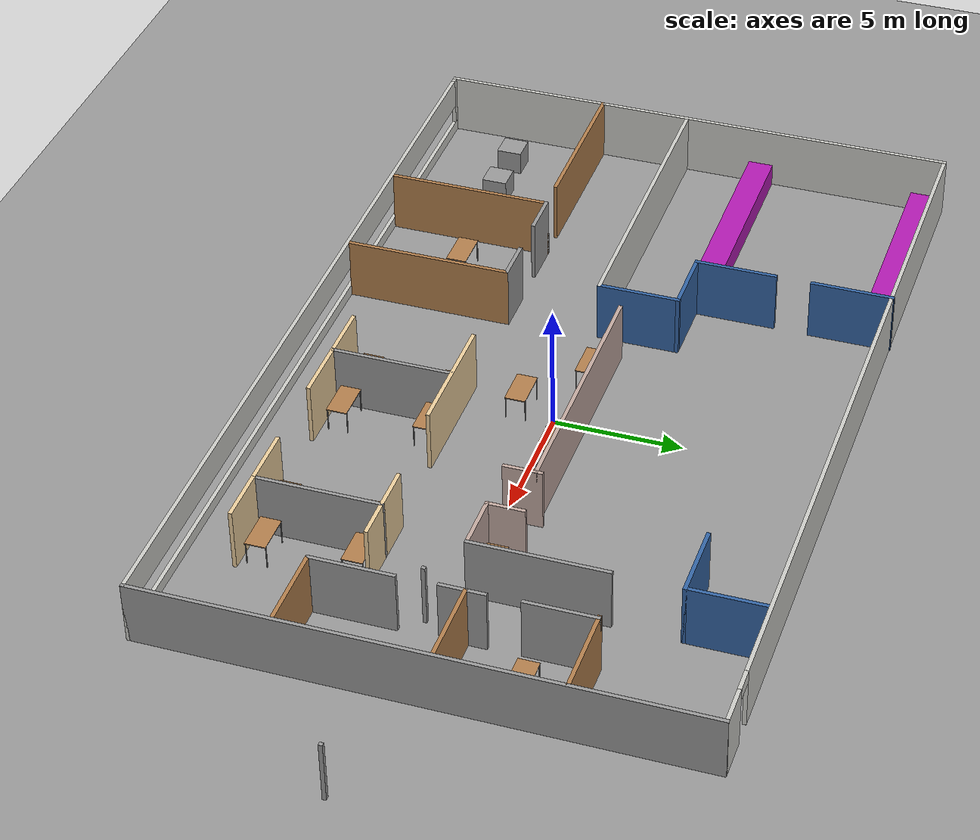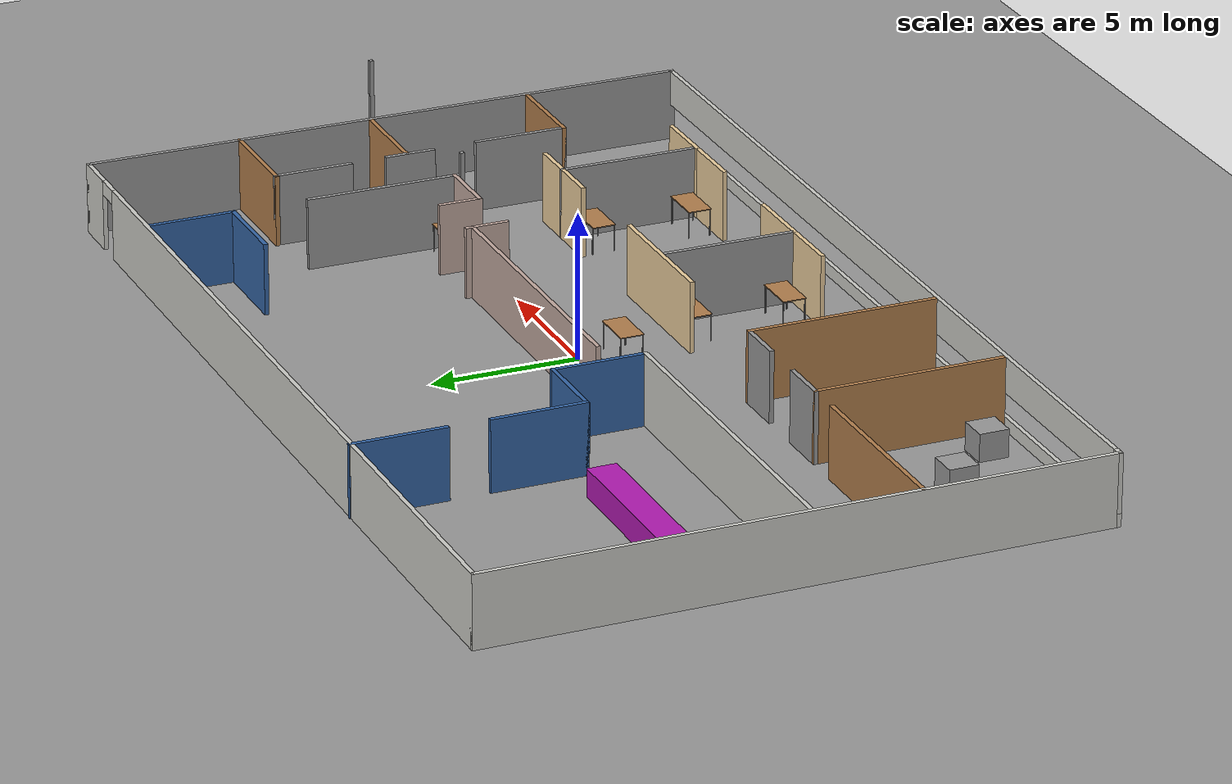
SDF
<sdf version="1.6">
 <world name="default">
  <light name="sun" type="directional">
   <pose>0 0 10 0 -0 0</pose>
   <diffuse>0.8 0.8 0.8 1</diffuse>
   <specular>0.2 0.2 0.2 1</specular>
   <attenuation>
    <range>1000</range>
    <constant>0.9</constant>
    <linear>0.01</linear>
    <quadratic>0.001</quadratic>
   </attenuation>
   <direction>-0.5 0.1 -0.9</direction>
  </light>
  <model name="ground_plane">
   <static>1</static>
   <link name="link">
    <collision name="collision">
     <geometry><plane><normal>0 0 1</normal><size>100 100</size></plane></geometry>
     <surface>
      <contact><collide_bitmask>65535</collide_bitmask></contact>
      <friction><ode><mu>100</mu><mu2>50</mu2></ode></friction>
     </surface>
    </collision>
    <visual name="visual">
     <cast_shadows>0</cast_shadows>
     <geometry><plane><normal>0 0 1</normal><size>100 100</size></plane></geometry>
     <material>
      <script><uri>file://media/materials/scripts/gazebo.material</uri><name>Gazebo/Grey</name></script>
     </material>
    </visual>
   </link>
  </model>
  <gravity>0 0 -9.8</gravity>
  <magnetic_field>6e-06 2.3e-05 -4.2e-05</magnetic_field>
  <atmosphere type="adiabatic"/>
  <physics name="default_physics" default="0" type="ode">
   <max_step_size>0.001</max_step_size>
   <real_time_factor>1</real_time_factor>
   <real_time_update_rate>1000</real_time_update_rate>
  </physics>
  <scene><ambient>0.4 0.4 0.4 1</ambient><background>0.7 0.7 0.7 1</background><shadows>1</shadows></scene>
  <audio><device>default</device></audio>
  <spherical_coordinates>
   <surface_model>EARTH_WGS84</surface_model>
   <latitude_deg>0</latitude_deg>
   <longitude_deg>0</longitude_deg>
   <elevation>0</elevation>
   <heading_deg>0</heading_deg>
  </spherical_coordinates>
  <model name="myworld2">
   <pose>1.34917 0.407472 0 0 -0 0</pose>
   <link name="Wall_21">
    <collision name="Wall_21_Collision">
     <geometry><box><size>0.15 0.15 2.5</size></box></geometry>
     <pose>0 0 1.25 0 -0 0</pose>
    </collision>
    <visual name="Wall_21_Visual">
     <pose>0 0 1.25 0 -0 0</pose>
     <geometry><box><size>0.15 0.15 2.5</size></box></geometry>
     <material>
      <script><uri>file://media/materials/scripts/gazebo.material</uri><name>Gazebo/Grey</name></script>
      <ambient>1 1 1 1</ambient>
     </material>
     <meta><layer>0</layer></meta>
    </visual>
    <pose>18.9712 -1.42144 0 0 -0 0</pose>
   </link>
   <link name="Wall_29">
    <collision name="Wall_29_Collision">
     <geometry><box><size>0.15 0.15 2.5</size></box></geometry>
     <pose>0 0 1.25 0 -0 0</pose>
    </collision>
    <visual name="Wall_29_Visual">
     <pose>0 0 1.25 0 -0 0</pose>
     <geometry><box><size>0.15 0.15 2.5</size></box></geometry>
     <material>
      <script><uri>file://media/materials/scripts/gazebo.material</uri><name>Gazebo/Grey</name></script>
      <ambient>1 1 1 1</ambient>
     </material>
     <meta><layer>0</layer></meta>
    </visual>
    <pose>10.2577 -1.19451 0 0 -0 0</pose>
   </link>
   <link name="Wall_32">
    <pose>-2.42121 10.4091 0 0 -0 0</pose>
    <visual name="Wall_32_Visual_0">
     <pose>-1.23336 0 1.25 0 -0 0</pose>
     <geometry><box><size>30.7833 0.15 2.5</size></box></geometry>
     <material>
      <script><uri>file://media/materials/scripts/gazebo.material</uri><name>Gazebo/CeilingTiled</name></script>
      <ambient>0.203922 0.396078 0.643137 1</ambient>
     </material>
     <meta><layer>0</layer></meta>
    </visual>
    <collision name="Wall_32_Collision_0">
     <geometry><box><size>30.7833 0.15 2.5</size></box></geometry>
     <pose>-1.23336 0 1.25 0 -0 0</pose>
    </collision>
    <visual name="Wall_32_Visual_1">
     <pose>15.8416 0 1.25 0 -0 0</pose>
     <geometry><box><size>1.56672 0.15 2.5</size></box></geometry>
     <material>
      <script><uri>file://media/materials/scripts/gazebo.material</uri><name>Gazebo/CeilingTiled</name></script>
      <ambient>0.203922 0.396078 0.643137 1</ambient>
     </material>
     <meta><layer>0</layer></meta>
    </visual>
    <collision name="Wall_32_Collision_1">
     <geometry><box><size>1.56672 0.15 2.5</size></box></geometry>
     <pose>15.8416 0 1.25 0 -0 0</pose>
    </collision>
    <visual name="Wall_32_Visual_2">
     <pose>14.6083 0 2.25 0 -0 0</pose>
     <geometry><box><size>0.9 0.15 0.5</size></box></geometry>
     <material>
      <script><uri>file://media/materials/scripts/gazebo.material</uri><name>Gazebo/CeilingTiled</name></script>
      <ambient>0.203922 0.396078 0.643137 1</ambient>
     </material>
     <meta><layer>0</layer></meta>
    </visual>
    <collision name="Wall_32_Collision_2">
     <geometry><box><size>0.9 0.15 0.5</size></box></geometry>
     <pose>14.6083 0 2.25 0 -0 0</pose>
    </collision>
   </link>
   <link name="Wall_33">
    <collision name="Wall_33_Collision">
     <geometry><box><size>21 0.15 2.5</size></box></geometry>
     <pose>0 0 1.25 0 -0 0</pose>
    </collision>
    <visual name="Wall_33_Visual">
     <pose>0 0 1.25 0 -0 0</pose>
     <geometry><box><size>21 0.15 2.5</size></box></geometry>
     <material>
      <script><uri>file://media/materials/scripts/gazebo.material</uri><name>Gazebo/Grey</name></script>
      <ambient>1 1 1 1</ambient>
     </material>
     <meta><layer>0</layer></meta>
    </visual>
    <pose>14.1288 -0.015902 0 0 -0 -1.5708</pose>
   </link>
   <link name="Wall_34">
    <pose>-2.42121 -10.4409 0 0 -0 3.14159</pose>
    <visual name="Wall_34_Visual_0">
     <pose>-16.5864 0 1.25 0 -0 0</pose>
     <geometry><box><size>0.077133 0.15 2.5</size></box></geometry>
     <material>
      <script><uri>file://media/materials/scripts/gazebo.material</uri><name>Gazebo/CeilingTiled</name></script>
      <ambient>1 1 1 1</ambient>
     </material>
     <meta><layer>0</layer></meta>
    </visual>
    <collision name="Wall_34_Collision_0">
     <geometry><box><size>0.077133 0.15 2.5</size></box></geometry>
     <pose>-16.5864 0 1.25 0 -0 0</pose>
    </collision>
    <visual name="Wall_34_Visual_1">
     <pose>0.038567 0 0.25 0 -0 0</pose>
     <geometry><box><size>33.1729 0.15 0.5</size></box></geometry>
     <material>
      <script><uri>file://media/materials/scripts/gazebo.material</uri><name>Gazebo/CeilingTiled</name></script>
      <ambient>1 1 1 1</ambient>
     </material>
     <meta><layer>0</layer></meta>
    </visual>
    <collision name="Wall_34_Collision_1">
     <geometry><box><size>33.1729 0.15 0.5</size></box></geometry>
     <pose>0.038567 0 0.25 0 -0 0</pose>
    </collision>
    <visual name="Wall_34_Visual_2">
     <pose>16.4492 0 1.5 0 -0 0</pose>
     <geometry><box><size>0.35158 0.15 2</size></box></geometry>
     <material>
      <script><uri>file://media/materials/scripts/gazebo.material</uri><name>Gazebo/CeilingTiled</name></script>
      <ambient>1 1 1 1</ambient>
     </material>
     <meta><layer>0</layer></meta>
    </visual>
    <collision name="Wall_34_Collision_2">
     <geometry><box><size>0.35158 0.15 2</size></box></geometry>
     <pose>16.4492 0 1.5 0 -0 0</pose>
    </collision>
    <visual name="Wall_34_Visual_3">
     <pose>-0.137223 0 1.9 0 -0 0</pose>
     <geometry><box><size>32.8213 0.15 1.2</size></box></geometry>
     <material>
      <script><uri>file://media/materials/scripts/gazebo.material</uri><name>Gazebo/CeilingTiled</name></script>
      <ambient>1 1 1 1</ambient>
     </material>
     <meta><layer>0</layer></meta>
    </visual>
    <collision name="Wall_34_Collision_3">
     <geometry><box><size>32.8213 0.15 1.2</size></box></geometry>
     <pose>-0.137223 0 1.9 0 -0 0</pose>
    </collision>
   </link>
   <link name="Wall_35">
    <collision name="Wall_35_Collision">
     <geometry><box><size>21 0.15 2.5</size></box></geometry>
     <pose>0 0 1.25 0 -0 0</pose>
    </collision>
    <visual name="Wall_35_Visual">
     <pose>0 0 1.25 0 -0 0</pose>
     <geometry><box><size>21 0.15 2.5</size></box></geometry>
     <material>
      <script><uri>file://media/materials/scripts/gazebo.material</uri><name>Gazebo/CeilingTiled</name></script>
      <ambient>1 1 1 1</ambient>
     </material>
     <meta><layer>0</layer></meta>
    </visual>
    <pose>-18.9712 -0.015902 0 0 -0 1.5708</pose>
   </link>
   <link name="Wall_38">
    <collision name="Wall_38_Collision">
     <geometry><box><size>6.5 0.15 2.5</size></box></geometry>
     <pose>0 0 1.25 0 -0 0</pose>
    </collision>
    <visual name="Wall_38_Visual">
     <pose>0 0 1.25 0 -0 0</pose>
     <geometry><box><size>6.5 0.15 2.5</size></box></geometry>
     <material>
      <script><uri>file://media/materials/scripts/gazebo.material</uri><name>Gazebo/Wood</name></script>
      <ambient>1 1 1 1</ambient>
     </material>
     <meta><layer>0</layer></meta>
    </visual>
    <pose>-15.7869 -3.95257 0 0 -0 0</pose>
   </link>
   <link name="Wall_40">
    <collision name="Wall_40_Collision">
     <geometry><box><size>1.75 0.15 2.5</size></box></geometry>
     <pose>0 0 1.25 0 -0 0</pose>
    </collision>
    <visual name="Wall_40_Visual">
     <pose>0 0 1.25 0 -0 0</pose>
     <geometry><box><size>1.75 0.15 2.5</size></box></geometry>
     <material>
      <script><uri>file://media/materials/scripts/gazebo.material</uri><name>Gazebo/Grey</name></script>
      <ambient>1 1 1 1</ambient>
     </material>
     <meta><layer>0</layer></meta>
    </visual>
    <pose>-10.5979 -3.95257 0 0 -0 0</pose>
   </link>
   <link name="Wall_42">
    <collision name="Wall_42_Collision">
     <geometry><box><size>1.75 0.15 2.5</size></box></geometry>
     <pose>0 0 1.25 0 -0 0</pose>
    </collision>
    <visual name="Wall_42_Visual">
     <pose>0 0 1.25 0 -0 0</pose>
     <geometry><box><size>1.75 0.15 2.5</size></box></geometry>
     <material>
      <script><uri>file://media/materials/scripts/gazebo.material</uri><name>Gazebo/Grey</name></script>
      <ambient>1 1 1 1</ambient>
     </material>
     <meta><layer>0</layer></meta>
    </visual>
    <pose>-7.34119 -3.95257 0 0 -0 0</pose>
   </link>
   <link name="Wall_44">
    <collision name="Wall_44_Collision">
     <geometry><box><size>6.5 0.15 2.5</size></box></geometry>
     <pose>0 0 1.25 0 -0 0</pose>
    </collision>
    <visual name="Wall_44_Visual">
     <pose>0 0 1.25 0 -0 0</pose>
     <geometry><box><size>6.5 0.15 2.5</size></box></geometry>
     <material>
      <script><uri>file://media/materials/scripts/gazebo.material</uri><name>Gazebo/Wood</name></script>
      <ambient>1 1 1 1</ambient>
     </material>
     <meta><layer>0</layer></meta>
    </visual>
    <pose>-6.54119 -7.12757 0 0 -0 -1.5708</pose>
   </link>
   <link name="Wall_46">
    <collision name="Wall_46_Collision">
     <geometry><box><size>6.5 0.15 2.5</size></box></geometry>
     <pose>0 0 1.25 0 -0 0</pose>
    </collision>
    <visual name="Wall_46_Visual">
     <pose>0 0 1.25 0 -0 0</pose>
     <geometry><box><size>6.5 0.15 2.5</size></box></geometry>
     <material>
      <script><uri>file://media/materials/scripts/gazebo.material</uri><name>Gazebo/Wood</name></script>
      <ambient>1 1 1 1</ambient>
     </material>
     <meta><layer>0</layer></meta>
    </visual>
    <pose>-11.3979 -7.12757 0 0 -0 -1.5708</pose>
   </link>
   <link name="Wall_48">
    <collision name="Wall_48_Collision">
     <geometry><box><size>12.25 0.15 2.5</size></box></geometry>
     <pose>0 0 1.25 0 -0 0</pose>
    </collision>
    <visual name="Wall_48_Visual">
     <pose>0 0 1.25 0 -0 0</pose>
     <geometry><box><size>12.25 0.15 2.5</size></box></geometry>
     <material>
      <script><uri>file://media/materials/scripts/gazebo.material</uri><name>Gazebo/CeilingTiled</name></script>
      <ambient>1 1 1 1</ambient>
     </material>
     <meta><layer>0</layer></meta>
    </visual>
    <pose>-12.8594 -0.328155 0 0 -0 0</pose>
   </link>
   <link name="Wall_49">
    <collision name="Wall_49_Collision">
     <geometry><box><size>3.25 0.15 2.5</size></box></geometry>
     <pose>0 0 1.25 0 -0 0</pose>
    </collision>
    <visual name="Wall_49_Visual">
     <pose>0 0 1.25 0 -0 0</pose>
     <geometry><box><size>3.25 0.15 2.5</size></box></geometry>
     <material>
      <script><uri>file://media/materials/scripts/gazebo.material</uri><name>Gazebo/Grey</name></script>
      <ambient>0.203922 0.396078 0.643137 1</ambient>
     </material>
     <meta><layer>0</layer></meta>
    </visual>
    <pose>-6.80939 1.22185 0 0 -0 1.5708</pose>
   </link>
   <link name="Wall_50">
    <collision name="Wall_50_Collision">
     <geometry><box><size>2.75 0.15 2.5</size></box></geometry>
     <pose>0 0 1.25 0 -0 0</pose>
    </collision>
    <visual name="Wall_50_Visual">
     <pose>0 0 1.25 0 -0 0</pose>
     <geometry><box><size>2.75 0.15 2.5</size></box></geometry>
     <material>
      <script><uri>file://media/materials/scripts/gazebo.material</uri><name>Gazebo/Grey</name></script>
      <ambient>0.203922 0.396078 0.643137 1</ambient>
     </material>
     <meta><layer>0</layer></meta>
    </visual>
    <pose>-8.10939 2.77184 0 0 -0 3.14159</pose>
   </link>
   <link name="Wall_53">
    <collision name="Wall_53_Collision">
     <geometry><box><size>3.25 0.15 2.5</size></box></geometry>
     <pose>0 0 1.25 0 -0 0</pose>
    </collision>
    <visual name="Wall_53_Visual">
     <pose>0 0 1.25 0 -0 0</pose>
     <geometry><box><size>3.25 0.15 2.5</size></box></geometry>
     <material>
      <script><uri>file://media/materials/scripts/gazebo.material</uri><name>Gazebo/Grey</name></script>
      <ambient>0.203922 0.396078 0.643137 1</ambient>
     </material>
     <meta><layer>0</layer></meta>
    </visual>
    <pose>-9.40939 4.32184 0 0 -0 1.5708</pose>
   </link>
   <link name="Wall_55">
    <collision name="Wall_55_Collision">
     <geometry><box><size>3.25 0.15 2.5</size></box></geometry>
     <pose>0 0 1.25 0 -0 0</pose>
    </collision>
    <visual name="Wall_55_Visual">
     <pose>0 0 1.25 0 -0 0</pose>
     <geometry><box><size>3.25 0.15 2.5</size></box></geometry>
     <material>
      <script><uri>file://media/materials/scripts/gazebo.material</uri><name>Gazebo/Grey</name></script>
      <ambient>0.203922 0.396078 0.643137 1</ambient>
     </material>
     <meta><layer>0</layer></meta>
    </visual>
    <pose>-9.40186 8.8909 0 0 -0 1.5708</pose>
   </link>
   <link name="Wall_57">
    <collision name="Wall_57_Collision">
     <geometry><box><size>10.25 0.15 2.5</size></box></geometry>
     <pose>0 1.5 1.25 0 -0 0</pose>
    </collision>
    <visual name="Wall_57_Visual">
     <pose>0 1.5 1.25 0 -0 0</pose>
     <geometry><box><size>10.25 0.15 2.5</size></box></geometry>
     <material>
      <script><uri>file://media/materials/scripts/gazebo.material</uri><name>Gazebo/Grey</name></script>
      <ambient>0.760784 0.662745 0.627451 1</ambient>
     </material>
     <meta><layer>0</layer></meta>
    </visual>
    <pose>-0.674915 -0.671847 0 0 -0 0</pose>
   </link>
   <link name="Wall_58">
    <collision name="Wall_58_Collision">
     <geometry><box><size>1.5 0.15 2.5</size></box></geometry>
     <pose>0 0 1.25 0 -0 0</pose>
    </collision>
    <visual name="Wall_58_Visual">
     <pose>0 0 1.25 0 -0 0</pose>
     <geometry><box><size>1.5 0.15 2.5</size></box></geometry>
     <material>
      <script><uri>file://media/materials/scripts/gazebo.material</uri><name>Gazebo/Grey</name></script>
      <ambient>0.760784 0.662745 0.627451 1</ambient>
     </material>
     <meta><layer>0</layer></meta>
    </visual>
    <pose>4.37509 0.346845 0 0 -0 1.5708</pose>
   </link>
   <link name="Wall_60">
    <collision name="Wall_60_Collision">
     <geometry><box><size>1.5 0.15 2.5</size></box></geometry>
     <pose>0 0 1.25 0 -0 0</pose>
    </collision>
    <visual name="Wall_60_Visual">
     <pose>0 0 1.25 0 -0 0</pose>
     <geometry><box><size>1.5 0.15 2.5</size></box></geometry>
     <material>
      <script><uri>file://media/materials/scripts/gazebo.material</uri><name>Gazebo/Grey</name></script>
      <ambient>0.760784 0.662745 0.627451 1</ambient>
     </material>
     <meta><layer>0</layer></meta>
    </visual>
    <pose>6.46153 0.415095 0 0 -0 -1.5708</pose>
   </link>
   <link name="Wall_61">
    <collision name="Wall_61_Collision">
     <geometry><box><size>2.25 0.15 2.5</size></box></geometry>
     <pose>0 0 1.25 0 -0 0</pose>
    </collision>
    <visual name="Wall_61_Visual">
     <pose>0 0 1.25 0 -0 0</pose>
     <geometry><box><size>2.25 0.15 2.5</size></box></geometry>
     <material>
      <script><uri>file://media/materials/scripts/gazebo.material</uri><name>Gazebo/Grey</name></script>
      <ambient>0.760784 0.662745 0.627451 1</ambient>
     </material>
     <meta><layer>0</layer></meta>
    </visual>
    <pose>7.51154 -0.259905 0 0 -0 0</pose>
   </link>
   <link name="Wall_62">
    <collision name="Wall_62_Collision">
     <geometry><box><size>5.25 0.15 2.5</size></box></geometry>
     <pose>0 0 1.25 0 -0 0</pose>
    </collision>
    <visual name="Wall_62_Visual">
     <pose>0 0 1.25 0 -0 0</pose>
     <geometry><box><size>5.25 0.15 2.5</size></box></geometry>
     <material>
      <script><uri>file://media/materials/scripts/gazebo.material</uri><name>Gazebo/Grey</name></script>
      <ambient>1 1 1 1</ambient>
     </material>
     <meta><layer>0</layer></meta>
    </visual>
    <pose>8.56154 2.29009 0 0 -0 1.5708</pose>
   </link>
   <link name="Wall_64">
    <collision name="Wall_64_Collision">
     <geometry><box><size>3 0.15 2.5</size></box></geometry>
     <pose>0 0 1.25 0 -0 0</pose>
    </collision>
    <visual name="Wall_64_Visual">
     <pose>0 0 1.25 0 -0 0</pose>
     <geometry><box><size>3 0.15 2.5</size></box></geometry>
     <material>
      <script><uri>file://media/materials/scripts/gazebo.material</uri><name>Gazebo/Grey</name></script>
      <ambient>0.203922 0.396078 0.643137 1</ambient>
     </material>
     <meta><layer>0</layer></meta>
    </visual>
    <pose>7.13765 7.44596 0 0 -0 3.14159</pose>
   </link>
   <link name="Wall_66">
    <collision name="Wall_66_Collision">
     <geometry><box><size>3 0.15 2.5</size></box></geometry>
     <pose>0 0 1.25 0 -0 0</pose>
    </collision>
    <visual name="Wall_66_Visual">
     <pose>0 0 1.25 0 -0 0</pose>
     <geometry><box><size>3 0.15 2.5</size></box></geometry>
     <material>
      <script><uri>file://media/materials/scripts/gazebo.material</uri><name>Gazebo/Grey</name></script>
      <ambient>0.203922 0.396078 0.643137 1</ambient>
     </material>
     <meta><layer>0</layer></meta>
    </visual>
    <pose>8.56265 8.87096 0 0 -0 1.5708</pose>
   </link>
   <link name="Wall_68">
    <collision name="Wall_68_Collision">
     <geometry><box><size>2.75 0.15 2.5</size></box></geometry>
     <pose>0 0 1.25 0 -0 0</pose>
    </collision>
    <visual name="Wall_68_Visual">
     <pose>0 0 1.25 0 -0 0</pose>
     <geometry><box><size>2.75 0.15 2.5</size></box></geometry>
     <material>
      <script><uri>file://media/materials/scripts/gazebo.material</uri><name>Gazebo/Grey</name></script>
      <ambient>1 1 1 1</ambient>
     </material>
     <meta><layer>0</layer></meta>
    </visual>
    <pose>10.8213 3.83474 0 0 -0 -1.5708</pose>
   </link>
   <link name="Wall_70">
    <collision name="Wall_70_Collision">
     <geometry><box><size>3.5 0.15 2.5</size></box></geometry>
     <pose>0 0 1.25 0 -0 0</pose>
    </collision>
    <visual name="Wall_70_Visual">
     <pose>0 0 1.25 0 -0 0</pose>
     <geometry><box><size>3.5 0.15 2.5</size></box></geometry>
     <material>
      <script><uri>file://media/materials/scripts/gazebo.material</uri><name>Gazebo/Wood</name></script>
      <ambient>1 1 1 1</ambient>
     </material>
     <meta><layer>0</layer></meta>
    </visual>
    <pose>12.4438 5.13474 0 0 -0 0</pose>
   </link>
   <link name="Wall_72">
    <collision name="Wall_72_Collision">
     <geometry><box><size>1.75 0.15 2.5</size></box></geometry>
     <pose>0 0 1.25 0 -0 0</pose>
    </collision>
    <visual name="Wall_72_Visual">
     <pose>0 0 1.25 0 -0 0</pose>
     <geometry><box><size>1.75 0.15 2.5</size></box></geometry>
     <material>
      <script><uri>file://media/materials/scripts/gazebo.material</uri><name>Gazebo/Grey</name></script>
      <ambient>1 1 1 1</ambient>
     </material>
     <meta><layer>0</layer></meta>
    </visual>
    <pose>10.8739 0.395151 0 0 -0 -1.5708</pose>
   </link>
   <link name="Wall_74">
    <collision name="Wall_74_Collision">
     <geometry><box><size>3.25 0.15 2.5</size></box></geometry>
     <pose>0 0 1.25 0 -0 0</pose>
    </collision>
    <visual name="Wall_74_Visual">
     <pose>0 0 1.25 0 -0 0</pose>
     <geometry><box><size>3.25 0.15 2.5</size></box></geometry>
     <material>
      <script><uri>file://media/materials/scripts/gazebo.material</uri><name>Gazebo/Grey</name></script>
      <ambient>1 1 1 1</ambient>
     </material>
     <meta><layer>0</layer></meta>
    </visual>
    <pose>10.9264 -3.55904 0 0 -0 -1.5708</pose>
   </link>
   <link name="Wall_75">
    <collision name="Wall_75_Collision">
     <geometry><box><size>3.25 0.15 2.5</size></box></geometry>
     <pose>0 0 1.25 0 -0 0</pose>
    </collision>
    <visual name="Wall_75_Visual">
     <pose>0 0 1.25 0 -0 0</pose>
     <geometry><box><size>3.25 0.15 2.5</size></box></geometry>
     <material>
      <script><uri>file://media/materials/scripts/gazebo.material</uri><name>Gazebo/Wood</name></script>
      <ambient>1 1 1 1</ambient>
     </material>
     <meta><layer>0</layer></meta>
    </visual>
    <pose>12.4764 -5.10905 0 0 -0 0</pose>
   </link>
   <link name="Wall_77">
    <collision name="Wall_77_Collision">
     <geometry><box><size>3.25 0.15 2.5</size></box></geometry>
     <pose>0 0 1.25 0 -0 0</pose>
    </collision>
    <visual name="Wall_77_Visual">
     <pose>0 0 1.25 0 -0 0</pose>
     <geometry><box><size>3.25 0.15 2.5</size></box></geometry>
     <material>
      <script><uri>file://media/materials/scripts/gazebo.material</uri><name>Gazebo/Wood</name></script>
      <ambient>1 1 1 1</ambient>
     </material>
     <meta><layer>0</layer></meta>
    </visual>
    <pose>12.4239 0.512289 0 0 -0 0</pose>
   </link>
   <link name="Wall_79">
    <collision name="Wall_79_Collision">
     <geometry><box><size>5 0.15 2.5</size></box></geometry>
     <pose>0 0 1.25 0 -0 0</pose>
    </collision>
    <visual name="Wall_79_Visual">
     <pose>0 0 1.25 0 -0 0</pose>
     <geometry><box><size>5 0.15 2.5</size></box></geometry>
     <material>
      <script><uri>file://media/materials/scripts/gazebo.material</uri><name>Gazebo/Grey</name></script>
      <ambient>0.921569 0.807843 0.615686 1</ambient>
     </material>
     <meta><layer>0</layer></meta>
    </visual>
    <pose>0.065808 -3.84752 0 0 -0 0</pose>
   </link>
   <link name="Wall_81">
    <collision name="Wall_81_Collision">
     <geometry><box><size>4.75 0.15 2.5</size></box></geometry>
     <pose>0 0 1.25 0 -0 0</pose>
    </collision>
    <visual name="Wall_81_Visual">
     <pose>0 0 1.25 0 -0 0</pose>
     <geometry><box><size>4.75 0.15 2.5</size></box></geometry>
     <material>
      <script><uri>file://media/materials/scripts/gazebo.material</uri><name>Gazebo/Grey</name></script>
      <ambient>1 1 1 1</ambient>
     </material>
     <meta><layer>0</layer></meta>
    </visual>
    <pose>0.000616 -6.20005 0 0 -0 -1.5708</pose>
   </link>
   <link name="Wall_82">
    <collision name="Wall_82_Collision">
     <geometry><box><size>2.5 0.15 2.5</size></box></geometry>
     <pose>0 0 1.25 0 -0 0</pose>
    </collision>
    <visual name="Wall_82_Visual">
     <pose>0 0 1.25 0 -0 0</pose>
     <geometry><box><size>2.5 0.15 2.5</size></box></geometry>
     <material>
      <script><uri>file://media/materials/scripts/gazebo.material</uri><name>Gazebo/Grey</name></script>
      <ambient>0.921569 0.807843 0.615686 1</ambient>
     </material>
     <meta><layer>0</layer></meta>
    </visual>
    <pose>1.17562 -8.50005 0 0 -0 0</pose>
   </link>
   <link name="Wall_84">
    <collision name="Wall_84_Collision">
     <geometry><box><size>2.25 0.15 2.5</size></box></geometry>
     <pose>0 0 1.25 0 -0 0</pose>
    </collision>
    <visual name="Wall_84_Visual">
     <pose>0 0 1.25 0 -0 0</pose>
     <geometry><box><size>2.25 0.15 2.5</size></box></geometry>
     <material>
      <script><uri>file://media/materials/scripts/gazebo.material</uri><name>Gazebo/Grey</name></script>
      <ambient>0.921569 0.807843 0.615686 1</ambient>
     </material>
     <meta><layer>0</layer></meta>
    </visual>
    <pose>-1.04938 -8.50005 0 0 -0 3.14159</pose>
   </link>
   <link name="Wall_86">
    <collision name="Wall_86_Collision">
     <geometry><box><size>3.25 0.15 2.5</size></box></geometry>
     <pose>0 0 1.25 0 -0 0</pose>
    </collision>
    <visual name="Wall_86_Visual">
     <pose>0 0 1.25 0 -0 0</pose>
     <geometry><box><size>3.25 0.15 2.5</size></box></geometry>
     <material>
      <script><uri>file://media/materials/scripts/gazebo.material</uri><name>Gazebo/Grey</name></script>
      <ambient>0.921569 0.807843 0.615686 1</ambient>
     </material>
     <meta><layer>0</layer></meta>
    </visual>
    <pose>7.53878 -3.68994 0 0 -0 0</pose>
   </link>
   <link name="Wall_88">
    <collision name="Wall_88_Collision">
     <geometry><box><size>4.75 0.15 2.5</size></box></geometry>
     <pose>0 0 1.25 0 -0 0</pose>
    </collision>
    <visual name="Wall_88_Visual">
     <pose>0 0 1.25 0 -0 0</pose>
     <geometry><box><size>4.75 0.15 2.5</size></box></geometry>
     <material>
      <script><uri>file://media/materials/scripts/gazebo.material</uri><name>Gazebo/Grey</name></script>
      <ambient>1 1 1 1</ambient>
     </material>
     <meta><layer>0</layer></meta>
    </visual>
    <pose>7.61715 -5.98994 0 0 -0 -1.5708</pose>
   </link>
   <link name="Wall_90">
    <collision name="Wall_90_Collision">
     <geometry><box><size>2.25 0.15 2.5</size></box></geometry>
     <pose>0 0 1.25 0 -0 0</pose>
    </collision>
    <visual name="Wall_90_Visual">
     <pose>0 0 1.25 0 -0 0</pose>
     <geometry><box><size>2.25 0.15 2.5</size></box></geometry>
     <material>
      <script><uri>file://media/materials/scripts/gazebo.material</uri><name>Gazebo/Grey</name></script>
      <ambient>0.921569 0.807843 0.615686 1</ambient>
     </material>
     <meta><layer>0</layer></meta>
    </visual>
    <pose>6.46098 -8.46997 0 0 -0 0</pose>
   </link>
   <link name="Wall_91">
    <collision name="Wall_91_Collision">
     <geometry><box><size>2.25 0.15 2.5</size></box></geometry>
     <pose>0 0 1.25 0 -0 0</pose>
    </collision>
    <visual name="Wall_91_Visual">
     <pose>0 0 1.25 0 -0 0</pose>
     <geometry><box><size>2.25 0.15 2.5</size></box></geometry>
     <material>
      <script><uri>file://media/materials/scripts/gazebo.material</uri><name>Gazebo/Grey</name></script>
      <ambient>0.921569 0.807843 0.615686 1</ambient>
     </material>
     <meta><layer>0</layer></meta>
    </visual>
    <pose>8.56098 -8.46997 0 0 -0 0</pose>
   </link>
   <static>1</static>
  </model>
  <model name="ground_plane_0">
   <static>1</static>
   <link name="link">
    <collision name="collision">
     <geometry><plane><normal>0 0 1</normal><size>100 100</size></plane></geometry>
     <surface>
      <contact><collide_bitmask>65535</collide_bitmask></contact>
      <friction><ode><mu>100</mu><mu2>50</mu2></ode></friction>
     </surface>
    </collision>
    <visual name="visual">
     <cast_shadows>0</cast_shadows>
     <geometry><plane><normal>0 0 1</normal><size>100 100</size></plane></geometry>
     <material>
      <script><uri>file://media/materials/scripts/gazebo.material</uri><name>Gazebo/Grey</name></script>
     </material>
    </visual>
   </link>
   <pose>-9.98437 5.08925 0 0 -0 0</pose>
  </model>
  <model name="table">
   <static>1</static>
   <link name="link">
    <collision name="surface">
     <pose>0 0 1 0 -0 0</pose>
     <geometry><box><size>1.5 0.8 0.03</size></box></geometry>
     <surface><friction><ode><mu>0.6</mu><mu2>0.6</mu2></ode></friction></surface>
    </collision>
    <visual name="visual1">
     <pose>0 0 1 0 -0 0</pose>
     <geometry><box><size>1.5 0.8 0.03</size></box></geometry>
     <material>
      <script><uri>file://media/materials/scripts/gazebo.material</uri><name>Gazebo/Wood</name></script>
     </material>
    </visual>
    <collision name="front_left_leg">
     <pose>0.68 0.38 0.5 0 -0 0</pose>
     <geometry><cylinder><radius>0.02</radius><length>1</length></cylinder></geometry>
    </collision>
    <visual name="front_left_leg">
     <pose>0.68 0.38 0.5 0 -0 0</pose>
     <geometry><cylinder><radius>0.02</radius><length>1</length></cylinder></geometry>
     <material>
      <script><uri>file://media/materials/scripts/gazebo.material</uri><name>Gazebo/Grey</name></script>
     </material>
    </visual>
    <collision name="front_right_leg">
     <pose>0.68 -0.38 0.5 0 -0 0</pose>
     <geometry><cylinder><radius>0.02</radius><length>1</length></cylinder></geometry>
    </collision>
    <visual name="front_right_leg">
     <pose>0.68 -0.38 0.5 0 -0 0</pose>
     <geometry><cylinder><radius>0.02</radius><length>1</length></cylinder></geometry>
     <material>
      <script><uri>file://media/materials/scripts/gazebo.material</uri><name>Gazebo/Grey</name></script>
     </material>
    </visual>
    <collision name="back_right_leg">
     <pose>-0.68 -0.38 0.5 0 -0 0</pose>
     <geometry><cylinder><radius>0.02</radius><length>1</length></cylinder></geometry>
    </collision>
    <visual name="back_right_leg">
     <pose>-0.68 -0.38 0.5 0 -0 0</pose>
     <geometry><cylinder><radius>0.02</radius><length>1</length></cylinder></geometry>
     <material>
      <script><uri>file://media/materials/scripts/gazebo.material</uri><name>Gazebo/Grey</name></script>
     </material>
    </visual>
    <collision name="back_left_leg">
     <pose>-0.68 0.38 0.5 0 -0 0</pose>
     <geometry><cylinder><radius>0.02</radius><length>1</length></cylinder></geometry>
    </collision>
    <visual name="back_left_leg">
     <pose>-0.68 0.38 0.5 0 -0 0</pose>
     <geometry><cylinder><radius>0.02</radius><length>1</length></cylinder></geometry>
     <material>
      <script><uri>file://media/materials/scripts/gazebo.material</uri><name>Gazebo/Grey</name></script>
     </material>
    </visual>
   </link>
   <pose>0.20374 -3.98405 0 0 -0 0</pose>
  </model>
  <model name="table_0">
   <static>1</static>
   <link name="link">
    <collision name="surface">
     <pose>0 0 1 0 -0 0</pose>
     <geometry><box><size>1.5 0.8 0.03</size></box></geometry>
     <surface><friction><ode><mu>0.6</mu><mu2>0.6</mu2></ode></friction></surface>
    </collision>
    <visual name="visual1">
     <pose>0 0 1 0 -0 0</pose>
     <geometry><box><size>1.5 0.8 0.03</size></box></geometry>
     <material>
      <script><uri>file://media/materials/scripts/gazebo.material</uri><name>Gazebo/Wood</name></script>
     </material>
    </visual>
    <collision name="front_left_leg">
     <pose>0.68 0.38 0.5 0 -0 0</pose>
     <geometry><cylinder><radius>0.02</radius><length>1</length></cylinder></geometry>
    </collision>
    <visual name="front_left_leg">
     <pose>0.68 0.38 0.5 0 -0 0</pose>
     <geometry><cylinder><radius>0.02</radius><length>1</length></cylinder></geometry>
     <material>
      <script><uri>file://media/materials/scripts/gazebo.material</uri><name>Gazebo/Grey</name></script>
     </material>
    </visual>
    <collision name="front_right_leg">
     <pose>0.68 -0.38 0.5 0 -0 0</pose>
     <geometry><cylinder><radius>0.02</radius><length>1</length></cylinder></geometry>
    </collision>
    <visual name="front_right_leg">
     <pose>0.68 -0.38 0.5 0 -0 0</pose>
     <geometry><cylinder><radius>0.02</radius><length>1</length></cylinder></geometry>
     <material>
      <script><uri>file://media/materials/scripts/gazebo.material</uri><name>Gazebo/Grey</name></script>
     </material>
    </visual>
    <collision name="back_right_leg">
     <pose>-0.68 -0.38 0.5 0 -0 0</pose>
     <geometry><cylinder><radius>0.02</radius><length>1</length></cylinder></geometry>
    </collision>
    <visual name="back_right_leg">
     <pose>-0.68 -0.38 0.5 0 -0 0</pose>
     <geometry><cylinder><radius>0.02</radius><length>1</length></cylinder></geometry>
     <material>
      <script><uri>file://media/materials/scripts/gazebo.material</uri><name>Gazebo/Grey</name></script>
     </material>
    </visual>
    <collision name="back_left_leg">
     <pose>-0.68 0.38 0.5 0 -0 0</pose>
     <geometry><cylinder><radius>0.02</radius><length>1</length></cylinder></geometry>
    </collision>
    <visual name="back_left_leg">
     <pose>-0.68 0.38 0.5 0 -0 0</pose>
     <geometry><cylinder><radius>0.02</radius><length>1</length></cylinder></geometry>
     <material>
      <script><uri>file://media/materials/scripts/gazebo.material</uri><name>Gazebo/Grey</name></script>
     </material>
    </visual>
   </link>
   <pose>4.6481 0.634532 0 0 -0 0</pose>
  </model>
  <model name="table_1">
   <static>1</static>
   <link name="link">
    <collision name="surface">
     <pose>0 0 1 0 -0 0</pose>
     <geometry><box><size>1.5 0.8 0.03</size></box></geometry>
     <surface><friction><ode><mu>0.6</mu><mu2>0.6</mu2></ode></friction></surface>
    </collision>
    <visual name="visual1">
     <pose>0 0 1 0 -0 0</pose>
     <geometry><box><size>1.5 0.8 0.03</size></box></geometry>
     <material>
      <script><uri>file://media/materials/scripts/gazebo.material</uri><name>Gazebo/Wood</name></script>
     </material>
    </visual>
    <collision name="front_left_leg">
     <pose>0.68 0.38 0.5 0 -0 0</pose>
     <geometry><cylinder><radius>0.02</radius><length>1</length></cylinder></geometry>
    </collision>
    <visual name="front_left_leg">
     <pose>0.68 0.38 0.5 0 -0 0</pose>
     <geometry><cylinder><radius>0.02</radius><length>1</length></cylinder></geometry>
     <material>
      <script><uri>file://media/materials/scripts/gazebo.material</uri><name>Gazebo/Grey</name></script>
     </material>
    </visual>
    <collision name="front_right_leg">
     <pose>0.68 -0.38 0.5 0 -0 0</pose>
     <geometry><cylinder><radius>0.02</radius><length>1</length></cylinder></geometry>
    </collision>
    <visual name="front_right_leg">
     <pose>0.68 -0.38 0.5 0 -0 0</pose>
     <geometry><cylinder><radius>0.02</radius><length>1</length></cylinder></geometry>
     <material>
      <script><uri>file://media/materials/scripts/gazebo.material</uri><name>Gazebo/Grey</name></script>
     </material>
    </visual>
    <collision name="back_right_leg">
     <pose>-0.68 -0.38 0.5 0 -0 0</pose>
     <geometry><cylinder><radius>0.02</radius><length>1</length></cylinder></geometry>
    </collision>
    <visual name="back_right_leg">
     <pose>-0.68 -0.38 0.5 0 -0 0</pose>
     <geometry><cylinder><radius>0.02</radius><length>1</length></cylinder></geometry>
     <material>
      <script><uri>file://media/materials/scripts/gazebo.material</uri><name>Gazebo/Grey</name></script>
     </material>
    </visual>
    <collision name="back_left_leg">
     <pose>-0.68 0.38 0.5 0 -0 0</pose>
     <geometry><cylinder><radius>0.02</radius><length>1</length></cylinder></geometry>
    </collision>
    <visual name="back_left_leg">
     <pose>-0.68 0.38 0.5 0 -0 0</pose>
     <geometry><cylinder><radius>0.02</radius><length>1</length></cylinder></geometry>
     <material>
      <script><uri>file://media/materials/scripts/gazebo.material</uri><name>Gazebo/Grey</name></script>
     </material>
    </visual>
   </link>
   <pose>2.07335 0.631478 0 0 -0 0</pose>
  </model>
  <model name="table_1_clone">
   <static>1</static>
   <link name="link">
    <collision name="surface">
     <pose>0 -2 1 0 -0 0</pose>
     <geometry><box><size>1.5 0.8 0.03</size></box></geometry>
     <surface><friction><ode><mu>0.6</mu><mu2>0.6</mu2></ode></friction></surface>
    </collision>
    <visual name="visual1">
     <pose>0 -2 1 0 -0 0</pose>
     <geometry><box><size>1.5 0.8 0.03</size></box></geometry>
     <material>
      <script><uri>file://media/materials/scripts/gazebo.material</uri><name>Gazebo/Wood</name></script>
     </material>
    </visual>
    <collision name="front_left_leg">
     <pose>0.68 -1.62 0.5 0 -0 0</pose>
     <geometry><cylinder><radius>0.02</radius><length>1</length></cylinder></geometry>
    </collision>
    <visual name="front_left_leg">
     <pose>0.68 -1.62 0.5 0 -0 0</pose>
     <geometry><cylinder><radius>0.02</radius><length>1</length></cylinder></geometry>
     <material>
      <script><uri>file://media/materials/scripts/gazebo.material</uri><name>Gazebo/Grey</name></script>
     </material>
    </visual>
    <collision name="front_right_leg">
     <pose>0.68 -2.38 0.5 0 -0 0</pose>
     <geometry><cylinder><radius>0.02</radius><length>1</length></cylinder></geometry>
    </collision>
    <visual name="front_right_leg">
     <pose>0.68 -2.38 0.5 0 -0 0</pose>
     <geometry><cylinder><radius>0.02</radius><length>1</length></cylinder></geometry>
     <material>
      <script><uri>file://media/materials/scripts/gazebo.material</uri><name>Gazebo/Grey</name></script>
     </material>
    </visual>
    <collision name="back_right_leg">
     <pose>-0.68 -2.38 0.5 0 -0 0</pose>
     <geometry><cylinder><radius>0.02</radius><length>1</length></cylinder></geometry>
    </collision>
    <visual name="back_right_leg">
     <pose>-0.68 -2.38 0.5 0 -0 0</pose>
     <geometry><cylinder><radius>0.02</radius><length>1</length></cylinder></geometry>
     <material>
      <script><uri>file://media/materials/scripts/gazebo.material</uri><name>Gazebo/Grey</name></script>
     </material>
    </visual>
    <collision name="back_left_leg">
     <pose>-0.68 -1.62 0.5 0 -0 0</pose>
     <geometry><cylinder><radius>0.02</radius><length>1</length></cylinder></geometry>
    </collision>
    <visual name="back_left_leg">
     <pose>-0.68 -1.62 0.5 0 -0 0</pose>
     <geometry><cylinder><radius>0.02</radius><length>1</length></cylinder></geometry>
     <material>
      <script><uri>file://media/materials/scripts/gazebo.material</uri><name>Gazebo/Grey</name></script>
     </material>
    </visual>
   </link>
   <pose>-0.381205 0.631998 0 0 -0 0</pose>
  </model>
  <model name="table_1_clone_0">
   <static>1</static>
   <link name="link">
    <collision name="surface">
     <pose>0 0 1 0 -0 0</pose>
     <geometry><box><size>1.5 0.8 0.03</size></box></geometry>
     <surface><friction><ode><mu>0.6</mu><mu2>0.6</mu2></ode></friction></surface>
    </collision>
    <visual name="visual1">
     <pose>0 0 1 0 -0 0</pose>
     <geometry><box><size>1.5 0.8 0.03</size></box></geometry>
     <material>
      <script><uri>file://media/materials/scripts/gazebo.material</uri><name>Gazebo/Wood</name></script>
     </material>
    </visual>
    <collision name="front_left_leg">
     <pose>0.68 0.38 0.5 0 -0 0</pose>
     <geometry><cylinder><radius>0.02</radius><length>1</length></cylinder></geometry>
    </collision>
    <visual name="front_left_leg">
     <pose>0.68 0.38 0.5 0 -0 0</pose>
     <geometry><cylinder><radius>0.02</radius><length>1</length></cylinder></geometry>
     <material>
      <script><uri>file://media/materials/scripts/gazebo.material</uri><name>Gazebo/Grey</name></script>
     </material>
    </visual>
    <collision name="front_right_leg">
     <pose>0.68 -0.38 0.5 0 -0 0</pose>
     <geometry><cylinder><radius>0.02</radius><length>1</length></cylinder></geometry>
    </collision>
    <visual name="front_right_leg">
     <pose>0.68 -0.38 0.5 0 -0 0</pose>
     <geometry><cylinder><radius>0.02</radius><length>1</length></cylinder></geometry>
     <material>
      <script><uri>file://media/materials/scripts/gazebo.material</uri><name>Gazebo/Grey</name></script>
     </material>
    </visual>
    <collision name="back_right_leg">
     <pose>-0.68 -0.38 0.5 0 -0 0</pose>
     <geometry><cylinder><radius>0.02</radius><length>1</length></cylinder></geometry>
    </collision>
    <visual name="back_right_leg">
     <pose>-0.68 -0.38 0.5 0 -0 0</pose>
     <geometry><cylinder><radius>0.02</radius><length>1</length></cylinder></geometry>
     <material>
      <script><uri>file://media/materials/scripts/gazebo.material</uri><name>Gazebo/Grey</name></script>
     </material>
    </visual>
    <collision name="back_left_leg">
     <pose>-0.68 0.38 0.5 0 -0 0</pose>
     <geometry><cylinder><radius>0.02</radius><length>1</length></cylinder></geometry>
    </collision>
    <visual name="back_left_leg">
     <pose>-0.68 0.38 0.5 0 -0 0</pose>
     <geometry><cylinder><radius>0.02</radius><length>1</length></cylinder></geometry>
     <material>
      <script><uri>file://media/materials/scripts/gazebo.material</uri><name>Gazebo/Grey</name></script>
     </material>
    </visual>
   </link>
   <pose>-2.72863 0.611935 0 0 -0 0</pose>
  </model>
  <model name="table_1_clone_1">
   <static>1</static>
   <link name="link">
    <collision name="surface">
     <pose>0 0 1 0 -0 0</pose>
     <geometry><box><size>1.5 0.8 0.03</size></box></geometry>
     <surface><friction><ode><mu>0.6</mu><mu2>0.6</mu2></ode></friction></surface>
    </collision>
    <visual name="visual1">
     <pose>0 0 1 0 -0 0</pose>
     <geometry><box><size>1.5 0.8 0.03</size></box></geometry>
     <material>
      <script><uri>file://media/materials/scripts/gazebo.material</uri><name>Gazebo/Wood</name></script>
     </material>
    </visual>
    <collision name="front_left_leg">
     <pose>0.68 0.38 0.5 0 -0 0</pose>
     <geometry><cylinder><radius>0.02</radius><length>1</length></cylinder></geometry>
    </collision>
    <visual name="front_left_leg">
     <pose>0.68 0.38 0.5 0 -0 0</pose>
     <geometry><cylinder><radius>0.02</radius><length>1</length></cylinder></geometry>
     <material>
      <script><uri>file://media/materials/scripts/gazebo.material</uri><name>Gazebo/Grey</name></script>
     </material>
    </visual>
    <collision name="front_right_leg">
     <pose>0.68 -0.38 0.5 0 -0 0</pose>
     <geometry><cylinder><radius>0.02</radius><length>1</length></cylinder></geometry>
    </collision>
    <visual name="front_right_leg">
     <pose>0.68 -0.38 0.5 0 -0 0</pose>
     <geometry><cylinder><radius>0.02</radius><length>1</length></cylinder></geometry>
     <material>
      <script><uri>file://media/materials/scripts/gazebo.material</uri><name>Gazebo/Grey</name></script>
     </material>
    </visual>
    <collision name="back_right_leg">
     <pose>-0.68 -0.38 0.5 0 -0 0</pose>
     <geometry><cylinder><radius>0.02</radius><length>1</length></cylinder></geometry>
    </collision>
    <visual name="back_right_leg">
     <pose>-0.68 -0.38 0.5 0 -0 0</pose>
     <geometry><cylinder><radius>0.02</radius><length>1</length></cylinder></geometry>
     <material>
      <script><uri>file://media/materials/scripts/gazebo.material</uri><name>Gazebo/Grey</name></script>
     </material>
    </visual>
    <collision name="back_left_leg">
     <pose>-0.68 0.38 0.5 0 -0 0</pose>
     <geometry><cylinder><radius>0.02</radius><length>1</length></cylinder></geometry>
    </collision>
    <visual name="back_left_leg">
     <pose>-0.68 0.38 0.5 0 -0 0</pose>
     <geometry><cylinder><radius>0.02</radius><length>1</length></cylinder></geometry>
     <material>
      <script><uri>file://media/materials/scripts/gazebo.material</uri><name>Gazebo/Grey</name></script>
     </material>
    </visual>
   </link>
   <pose>2.22704 -4.02272 0 0 -0 0</pose>
  </model>
  <model name="table_1_clone_2">
   <static>1</static>
   <link name="link">
    <collision name="surface">
     <pose>0 0 1 0 -0 0</pose>
     <geometry><box><size>1.5 0.8 0.03</size></box></geometry>
     <surface><friction><ode><mu>0.6</mu><mu2>0.6</mu2></ode></friction></surface>
    </collision>
    <visual name="visual1">
     <pose>0 0 1 0 -0 0</pose>
     <geometry><box><size>1.5 0.8 0.03</size></box></geometry>
     <material>
      <script><uri>file://media/materials/scripts/gazebo.material</uri><name>Gazebo/Wood</name></script>
     </material>
    </visual>
    <collision name="front_left_leg">
     <pose>0.68 0.38 0.5 0 -0 0</pose>
     <geometry><cylinder><radius>0.02</radius><length>1</length></cylinder></geometry>
    </collision>
    <visual name="front_left_leg">
     <pose>0.68 0.38 0.5 0 -0 0</pose>
     <geometry><cylinder><radius>0.02</radius><length>1</length></cylinder></geometry>
     <material>
      <script><uri>file://media/materials/scripts/gazebo.material</uri><name>Gazebo/Grey</name></script>
     </material>
    </visual>
    <collision name="front_right_leg">
     <pose>0.68 -0.38 0.5 0 -0 0</pose>
     <geometry><cylinder><radius>0.02</radius><length>1</length></cylinder></geometry>
    </collision>
    <visual name="front_right_leg">
     <pose>0.68 -0.38 0.5 0 -0 0</pose>
     <geometry><cylinder><radius>0.02</radius><length>1</length></cylinder></geometry>
     <material>
      <script><uri>file://media/materials/scripts/gazebo.material</uri><name>Gazebo/Grey</name></script>
     </material>
    </visual>
    <collision name="back_right_leg">
     <pose>-0.68 -0.38 0.5 0 -0 0</pose>
     <geometry><cylinder><radius>0.02</radius><length>1</length></cylinder></geometry>
    </collision>
    <visual name="back_right_leg">
     <pose>-0.68 -0.38 0.5 0 -0 0</pose>
     <geometry><cylinder><radius>0.02</radius><length>1</length></cylinder></geometry>
     <material>
      <script><uri>file://media/materials/scripts/gazebo.material</uri><name>Gazebo/Grey</name></script>
     </material>
    </visual>
    <collision name="back_left_leg">
     <pose>-0.68 0.38 0.5 0 -0 0</pose>
     <geometry><cylinder><radius>0.02</radius><length>1</length></cylinder></geometry>
    </collision>
    <visual name="back_left_leg">
     <pose>-0.68 0.38 0.5 0 -0 0</pose>
     <geometry><cylinder><radius>0.02</radius><length>1</length></cylinder></geometry>
     <material>
      <script><uri>file://media/materials/scripts/gazebo.material</uri><name>Gazebo/Grey</name></script>
     </material>
    </visual>
   </link>
   <pose>2.26716 -7.37331 0 0 -0 0</pose>
  </model>
  <model name="table_1_clone_3">
   <static>1</static>
   <link name="link">
    <collision name="surface">
     <pose>0 0 1 0 -0 0</pose>
     <geometry><box><size>1.5 0.8 0.03</size></box></geometry>
     <surface><friction><ode><mu>0.6</mu><mu2>0.6</mu2></ode></friction></surface>
    </collision>
    <visual name="visual1">
     <pose>0 0 1 0 -0 0</pose>
     <geometry><box><size>1.5 0.8 0.03</size></box></geometry>
     <material>
      <script><uri>file://media/materials/scripts/gazebo.material</uri><name>Gazebo/Wood</name></script>
     </material>
    </visual>
    <collision name="front_left_leg">
     <pose>0.68 0.38 0.5 0 -0 0</pose>
     <geometry><cylinder><radius>0.02</radius><length>1</length></cylinder></geometry>
    </collision>
    <visual name="front_left_leg">
     <pose>0.68 0.38 0.5 0 -0 0</pose>
     <geometry><cylinder><radius>0.02</radius><length>1</length></cylinder></geometry>
     <material>
      <script><uri>file://media/materials/scripts/gazebo.material</uri><name>Gazebo/Grey</name></script>
     </material>
    </visual>
    <collision name="front_right_leg">
     <pose>0.68 -0.38 0.5 0 -0 0</pose>
     <geometry><cylinder><radius>0.02</radius><length>1</length></cylinder></geometry>
    </collision>
    <visual name="front_right_leg">
     <pose>0.68 -0.38 0.5 0 -0 0</pose>
     <geometry><cylinder><radius>0.02</radius><length>1</length></cylinder></geometry>
     <material>
      <script><uri>file://media/materials/scripts/gazebo.material</uri><name>Gazebo/Grey</name></script>
     </material>
    </visual>
    <collision name="back_right_leg">
     <pose>-0.68 -0.38 0.5 0 -0 0</pose>
     <geometry><cylinder><radius>0.02</radius><length>1</length></cylinder></geometry>
    </collision>
    <visual name="back_right_leg">
     <pose>-0.68 -0.38 0.5 0 -0 0</pose>
     <geometry><cylinder><radius>0.02</radius><length>1</length></cylinder></geometry>
     <material>
      <script><uri>file://media/materials/scripts/gazebo.material</uri><name>Gazebo/Grey</name></script>
     </material>
    </visual>
    <collision name="back_left_leg">
     <pose>-0.68 0.38 0.5 0 -0 0</pose>
     <geometry><cylinder><radius>0.02</radius><length>1</length></cylinder></geometry>
    </collision>
    <visual name="back_left_leg">
     <pose>-0.68 0.38 0.5 0 -0 0</pose>
     <geometry><cylinder><radius>0.02</radius><length>1</length></cylinder></geometry>
     <material>
      <script><uri>file://media/materials/scripts/gazebo.material</uri><name>Gazebo/Grey</name></script>
     </material>
    </visual>
   </link>
   <pose>0.18057 -7.25293 0 0 -0 0</pose>
  </model>
  <model name="table_1_clone_4">
   <static>1</static>
   <link name="link">
    <collision name="surface">
     <pose>0 0 1 0 -0 0</pose>
     <geometry><box><size>1.5 0.8 0.03</size></box></geometry>
     <surface><friction><ode><mu>0.6</mu><mu2>0.6</mu2></ode></friction></surface>
    </collision>
    <visual name="visual1">
     <pose>0 0 1 0 -0 0</pose>
     <geometry><box><size>1.5 0.8 0.03</size></box></geometry>
     <material>
      <script><uri>file://media/materials/scripts/gazebo.material</uri><name>Gazebo/Wood</name></script>
     </material>
    </visual>
    <collision name="front_left_leg">
     <pose>0.68 0.38 0.5 0 -0 0</pose>
     <geometry><cylinder><radius>0.02</radius><length>1</length></cylinder></geometry>
    </collision>
    <visual name="front_left_leg">
     <pose>0.68 0.38 0.5 0 -0 0</pose>
     <geometry><cylinder><radius>0.02</radius><length>1</length></cylinder></geometry>
     <material>
      <script><uri>file://media/materials/scripts/gazebo.material</uri><name>Gazebo/Grey</name></script>
     </material>
    </visual>
    <collision name="front_right_leg">
     <pose>0.68 -0.38 0.5 0 -0 0</pose>
     <geometry><cylinder><radius>0.02</radius><length>1</length></cylinder></geometry>
    </collision>
    <visual name="front_right_leg">
     <pose>0.68 -0.38 0.5 0 -0 0</pose>
     <geometry><cylinder><radius>0.02</radius><length>1</length></cylinder></geometry>
     <material>
      <script><uri>file://media/materials/scripts/gazebo.material</uri><name>Gazebo/Grey</name></script>
     </material>
    </visual>
    <collision name="back_right_leg">
     <pose>-0.68 -0.38 0.5 0 -0 0</pose>
     <geometry><cylinder><radius>0.02</radius><length>1</length></cylinder></geometry>
    </collision>
    <visual name="back_right_leg">
     <pose>-0.68 -0.38 0.5 0 -0 0</pose>
     <geometry><cylinder><radius>0.02</radius><length>1</length></cylinder></geometry>
     <material>
      <script><uri>file://media/materials/scripts/gazebo.material</uri><name>Gazebo/Grey</name></script>
     </material>
    </visual>
    <collision name="back_left_leg">
     <pose>-0.68 0.38 0.5 0 -0 0</pose>
     <geometry><cylinder><radius>0.02</radius><length>1</length></cylinder></geometry>
    </collision>
    <visual name="back_left_leg">
     <pose>-0.68 0.38 0.5 0 -0 0</pose>
     <geometry><cylinder><radius>0.02</radius><length>1</length></cylinder></geometry>
     <material>
      <script><uri>file://media/materials/scripts/gazebo.material</uri><name>Gazebo/Grey</name></script>
     </material>
    </visual>
   </link>
   <pose>7.98789 -7.43447 0 0 -0 0</pose>
  </model>
  <model name="table_1_clone_5">
   <static>1</static>
   <link name="link">
    <collision name="surface">
     <pose>0 0 1 0 -0 0</pose>
     <geometry><box><size>1.5 0.8 0.03</size></box></geometry>
     <surface><friction><ode><mu>0.6</mu><mu2>0.6</mu2></ode></friction></surface>
    </collision>
    <visual name="visual1">
     <pose>0 0 1 0 -0 0</pose>
     <geometry><box><size>1.5 0.8 0.03</size></box></geometry>
     <material>
      <script><uri>file://media/materials/scripts/gazebo.material</uri><name>Gazebo/Wood</name></script>
     </material>
    </visual>
    <collision name="front_left_leg">
     <pose>0.68 0.38 0.5 0 -0 0</pose>
     <geometry><cylinder><radius>0.02</radius><length>1</length></cylinder></geometry>
    </collision>
    <visual name="front_left_leg">
     <pose>0.68 0.38 0.5 0 -0 0</pose>
     <geometry><cylinder><radius>0.02</radius><length>1</length></cylinder></geometry>
     <material>
      <script><uri>file://media/materials/scripts/gazebo.material</uri><name>Gazebo/Grey</name></script>
     </material>
    </visual>
    <collision name="front_right_leg">
     <pose>0.68 -0.38 0.5 0 -0 0</pose>
     <geometry><cylinder><radius>0.02</radius><length>1</length></cylinder></geometry>
    </collision>
    <visual name="front_right_leg">
     <pose>0.68 -0.38 0.5 0 -0 0</pose>
     <geometry><cylinder><radius>0.02</radius><length>1</length></cylinder></geometry>
     <material>
      <script><uri>file://media/materials/scripts/gazebo.material</uri><name>Gazebo/Grey</name></script>
     </material>
    </visual>
    <collision name="back_right_leg">
     <pose>-0.68 -0.38 0.5 0 -0 0</pose>
     <geometry><cylinder><radius>0.02</radius><length>1</length></cylinder></geometry>
    </collision>
    <visual name="back_right_leg">
     <pose>-0.68 -0.38 0.5 0 -0 0</pose>
     <geometry><cylinder><radius>0.02</radius><length>1</length></cylinder></geometry>
     <material>
      <script><uri>file://media/materials/scripts/gazebo.material</uri><name>Gazebo/Grey</name></script>
     </material>
    </visual>
    <collision name="back_left_leg">
     <pose>-0.68 0.38 0.5 0 -0 0</pose>
     <geometry><cylinder><radius>0.02</radius><length>1</length></cylinder></geometry>
    </collision>
    <visual name="back_left_leg">
     <pose>-0.68 0.38 0.5 0 -0 0</pose>
     <geometry><cylinder><radius>0.02</radius><length>1</length></cylinder></geometry>
     <material>
      <script><uri>file://media/materials/scripts/gazebo.material</uri><name>Gazebo/Grey</name></script>
     </material>
    </visual>
   </link>
   <pose>10.0344 -7.35421 0 0 -0 0</pose>
  </model>
  <model name="table_1_clone_6">
   <static>1</static>
   <link name="link">
    <collision name="surface">
     <pose>0 0 1 0 -0 0</pose>
     <geometry><box><size>1.5 0.8 0.03</size></box></geometry>
     <surface><friction><ode><mu>0.6</mu><mu2>0.6</mu2></ode></friction></surface>
    </collision>
    <visual name="visual1">
     <pose>0 0 1 0 -0 0</pose>
     <geometry><box><size>1.5 0.8 0.03</size></box></geometry>
     <material>
      <script><uri>file://media/materials/scripts/gazebo.material</uri><name>Gazebo/Wood</name></script>
     </material>
    </visual>
    <collision name="front_left_leg">
     <pose>0.68 0.38 0.5 0 -0 0</pose>
     <geometry><cylinder><radius>0.02</radius><length>1</length></cylinder></geometry>
    </collision>
    <visual name="front_left_leg">
     <pose>0.68 0.38 0.5 0 -0 0</pose>
     <geometry><cylinder><radius>0.02</radius><length>1</length></cylinder></geometry>
     <material>
      <script><uri>file://media/materials/scripts/gazebo.material</uri><name>Gazebo/Grey</name></script>
     </material>
    </visual>
    <collision name="front_right_leg">
     <pose>0.68 -0.38 0.5 0 -0 0</pose>
     <geometry><cylinder><radius>0.02</radius><length>1</length></cylinder></geometry>
    </collision>
    <visual name="front_right_leg">
     <pose>0.68 -0.38 0.5 0 -0 0</pose>
     <geometry><cylinder><radius>0.02</radius><length>1</length></cylinder></geometry>
     <material>
      <script><uri>file://media/materials/scripts/gazebo.material</uri><name>Gazebo/Grey</name></script>
     </material>
    </visual>
    <collision name="back_right_leg">
     <pose>-0.68 -0.38 0.5 0 -0 0</pose>
     <geometry><cylinder><radius>0.02</radius><length>1</length></cylinder></geometry>
    </collision>
    <visual name="back_right_leg">
     <pose>-0.68 -0.38 0.5 0 -0 0</pose>
     <geometry><cylinder><radius>0.02</radius><length>1</length></cylinder></geometry>
     <material>
      <script><uri>file://media/materials/scripts/gazebo.material</uri><name>Gazebo/Grey</name></script>
     </material>
    </visual>
    <collision name="back_left_leg">
     <pose>-0.68 0.38 0.5 0 -0 0</pose>
     <geometry><cylinder><radius>0.02</radius><length>1</length></cylinder></geometry>
    </collision>
    <visual name="back_left_leg">
     <pose>-0.68 0.38 0.5 0 -0 0</pose>
     <geometry><cylinder><radius>0.02</radius><length>1</length></cylinder></geometry>
     <material>
      <script><uri>file://media/materials/scripts/gazebo.material</uri><name>Gazebo/Grey</name></script>
     </material>
    </visual>
   </link>
   <pose>9.7735 -3.86318 0 0 -0 0</pose>
  </model>
  <model name="table_1_clone_7">
   <static>1</static>
   <link name="link">
    <collision name="surface">
     <pose>0 0 1 0 -0 0</pose>
     <geometry><box><size>1.5 0.8 0.03</size></box></geometry>
     <surface><friction><ode><mu>0.6</mu><mu2>0.6</mu2></ode></friction></surface>
    </collision>
    <visual name="visual1">
     <pose>0 0 1 0 -0 0</pose>
     <geometry><box><size>1.5 0.8 0.03</size></box></geometry>
     <material>
      <script><uri>file://media/materials/scripts/gazebo.material</uri><name>Gazebo/Wood</name></script>
     </material>
    </visual>
    <collision name="front_left_leg">
     <pose>0.68 0.38 0.5 0 -0 0</pose>
     <geometry><cylinder><radius>0.02</radius><length>1</length></cylinder></geometry>
    </collision>
    <visual name="front_left_leg">
     <pose>0.68 0.38 0.5 0 -0 0</pose>
     <geometry><cylinder><radius>0.02</radius><length>1</length></cylinder></geometry>
     <material>
      <script><uri>file://media/materials/scripts/gazebo.material</uri><name>Gazebo/Grey</name></script>
     </material>
    </visual>
    <collision name="front_right_leg">
     <pose>0.68 -0.38 0.5 0 -0 0</pose>
     <geometry><cylinder><radius>0.02</radius><length>1</length></cylinder></geometry>
    </collision>
    <visual name="front_right_leg">
     <pose>0.68 -0.38 0.5 0 -0 0</pose>
     <geometry><cylinder><radius>0.02</radius><length>1</length></cylinder></geometry>
     <material>
      <script><uri>file://media/materials/scripts/gazebo.material</uri><name>Gazebo/Grey</name></script>
     </material>
    </visual>
    <collision name="back_right_leg">
     <pose>-0.68 -0.38 0.5 0 -0 0</pose>
     <geometry><cylinder><radius>0.02</radius><length>1</length></cylinder></geometry>
    </collision>
    <visual name="back_right_leg">
     <pose>-0.68 -0.38 0.5 0 -0 0</pose>
     <geometry><cylinder><radius>0.02</radius><length>1</length></cylinder></geometry>
     <material>
      <script><uri>file://media/materials/scripts/gazebo.material</uri><name>Gazebo/Grey</name></script>
     </material>
    </visual>
    <collision name="back_left_leg">
     <pose>-0.68 0.38 0.5 0 -0 0</pose>
     <geometry><cylinder><radius>0.02</radius><length>1</length></cylinder></geometry>
    </collision>
    <visual name="back_left_leg">
     <pose>-0.68 0.38 0.5 0 -0 0</pose>
     <geometry><cylinder><radius>0.02</radius><length>1</length></cylinder></geometry>
     <material>
      <script><uri>file://media/materials/scripts/gazebo.material</uri><name>Gazebo/Grey</name></script>
     </material>
    </visual>
   </link>
   <pose>8.02795 -4.02369 0 0 -0 0</pose>
  </model>
  <model name="table_1_clone_8">
   <static>1</static>
   <link name="link">
    <collision name="surface">
     <pose>0 0 1 0 -0 0</pose>
     <geometry><box><size>1.5 0.8 0.03</size></box></geometry>
     <surface><friction><ode><mu>0.6</mu><mu2>0.6</mu2></ode></friction></surface>
    </collision>
    <visual name="visual1">
     <pose>0 0 1 0 -0 0</pose>
     <geometry><box><size>1.5 0.8 0.03</size></box></geometry>
     <material>
      <script><uri>file://media/materials/scripts/gazebo.material</uri><name>Gazebo/Wood</name></script>
     </material>
    </visual>
    <collision name="front_left_leg">
     <pose>0.68 0.38 0.5 0 -0 0</pose>
     <geometry><cylinder><radius>0.02</radius><length>1</length></cylinder></geometry>
    </collision>
    <visual name="front_left_leg">
     <pose>0.68 0.38 0.5 0 -0 0</pose>
     <geometry><cylinder><radius>0.02</radius><length>1</length></cylinder></geometry>
     <material>
      <script><uri>file://media/materials/scripts/gazebo.material</uri><name>Gazebo/Grey</name></script>
     </material>
    </visual>
    <collision name="front_right_leg">
     <pose>0.68 -0.38 0.5 0 -0 0</pose>
     <geometry><cylinder><radius>0.02</radius><length>1</length></cylinder></geometry>
    </collision>
    <visual name="front_right_leg">
     <pose>0.68 -0.38 0.5 0 -0 0</pose>
     <geometry><cylinder><radius>0.02</radius><length>1</length></cylinder></geometry>
     <material>
      <script><uri>file://media/materials/scripts/gazebo.material</uri><name>Gazebo/Grey</name></script>
     </material>
    </visual>
    <collision name="back_right_leg">
     <pose>-0.68 -0.38 0.5 0 -0 0</pose>
     <geometry><cylinder><radius>0.02</radius><length>1</length></cylinder></geometry>
    </collision>
    <visual name="back_right_leg">
     <pose>-0.68 -0.38 0.5 0 -0 0</pose>
     <geometry><cylinder><radius>0.02</radius><length>1</length></cylinder></geometry>
     <material>
      <script><uri>file://media/materials/scripts/gazebo.material</uri><name>Gazebo/Grey</name></script>
     </material>
    </visual>
    <collision name="back_left_leg">
     <pose>-0.68 0.38 0.5 0 -0 0</pose>
     <geometry><cylinder><radius>0.02</radius><length>1</length></cylinder></geometry>
    </collision>
    <visual name="back_left_leg">
     <pose>-0.68 0.38 0.5 0 -0 0</pose>
     <geometry><cylinder><radius>0.02</radius><length>1</length></cylinder></geometry>
     <material>
      <script><uri>file://media/materials/scripts/gazebo.material</uri><name>Gazebo/Grey</name></script>
     </material>
    </visual>
   </link>
   <pose>8.93083 0.651093 0 0 -0 0</pose>
  </model>
  <model name="table_1_clone_9">
   <static>1</static>
   <link name="link">
    <collision name="surface">
     <pose>0 0 1 0 -0 0</pose>
     <geometry><box><size>1.5 0.8 0.03</size></box></geometry>
     <surface><friction><ode><mu>0.6</mu><mu2>0.6</mu2></ode></friction></surface>
    </collision>
    <visual name="visual1">
     <pose>0 0 1 0 -0 0</pose>
     <geometry><box><size>1.5 0.8 0.03</size></box></geometry>
     <material>
      <script><uri>file://media/materials/scripts/gazebo.material</uri><name>Gazebo/Wood</name></script>
     </material>
    </visual>
    <collision name="front_left_leg">
     <pose>0.68 0.38 0.5 0 -0 0</pose>
     <geometry><cylinder><radius>0.02</radius><length>1</length></cylinder></geometry>
    </collision>
    <visual name="front_left_leg">
     <pose>0.68 0.38 0.5 0 -0 0</pose>
     <geometry><cylinder><radius>0.02</radius><length>1</length></cylinder></geometry>
     <material>
      <script><uri>file://media/materials/scripts/gazebo.material</uri><name>Gazebo/Grey</name></script>
     </material>
    </visual>
    <collision name="front_right_leg">
     <pose>0.68 -0.38 0.5 0 -0 0</pose>
     <geometry><cylinder><radius>0.02</radius><length>1</length></cylinder></geometry>
    </collision>
    <visual name="front_right_leg">
     <pose>0.68 -0.38 0.5 0 -0 0</pose>
     <geometry><cylinder><radius>0.02</radius><length>1</length></cylinder></geometry>
     <material>
      <script><uri>file://media/materials/scripts/gazebo.material</uri><name>Gazebo/Grey</name></script>
     </material>
    </visual>
    <collision name="back_right_leg">
     <pose>-0.68 -0.38 0.5 0 -0 0</pose>
     <geometry><cylinder><radius>0.02</radius><length>1</length></cylinder></geometry>
    </collision>
    <visual name="back_right_leg">
     <pose>-0.68 -0.38 0.5 0 -0 0</pose>
     <geometry><cylinder><radius>0.02</radius><length>1</length></cylinder></geometry>
     <material>
      <script><uri>file://media/materials/scripts/gazebo.material</uri><name>Gazebo/Grey</name></script>
     </material>
    </visual>
    <collision name="back_left_leg">
     <pose>-0.68 0.38 0.5 0 -0 0</pose>
     <geometry><cylinder><radius>0.02</radius><length>1</length></cylinder></geometry>
    </collision>
    <visual name="back_left_leg">
     <pose>-0.68 0.38 0.5 0 -0 0</pose>
     <geometry><cylinder><radius>0.02</radius><length>1</length></cylinder></geometry>
     <material>
      <script><uri>file://media/materials/scripts/gazebo.material</uri><name>Gazebo/Grey</name></script>
     </material>
    </visual>
   </link>
   <pose>14.0672 3.50019 0 0 -0 0</pose>
  </model>
  <model name="table_1_clone_10">
   <static>1</static>
   <link name="link">
    <collision name="surface">
     <pose>0 0 1 0 -0 0</pose>
     <geometry><box><size>1.5 0.8 0.03</size></box></geometry>
     <surface><friction><ode><mu>0.6</mu><mu2>0.6</mu2></ode></friction></surface>
    </collision>
    <visual name="visual1">
     <pose>0 0 1 0 -0 0</pose>
     <geometry><box><size>1.5 0.8 0.03</size></box></geometry>
     <material>
      <script><uri>file://media/materials/scripts/gazebo.material</uri><name>Gazebo/Wood</name></script>
     </material>
    </visual>
    <collision name="front_left_leg">
     <pose>0.68 0.38 0.5 0 -0 0</pose>
     <geometry><cylinder><radius>0.02</radius><length>1</length></cylinder></geometry>
    </collision>
    <visual name="front_left_leg">
     <pose>0.68 0.38 0.5 0 -0 0</pose>
     <geometry><cylinder><radius>0.02</radius><length>1</length></cylinder></geometry>
     <material>
      <script><uri>file://media/materials/scripts/gazebo.material</uri><name>Gazebo/Grey</name></script>
     </material>
    </visual>
    <collision name="front_right_leg">
     <pose>0.68 -0.38 0.5 0 -0 0</pose>
     <geometry><cylinder><radius>0.02</radius><length>1</length></cylinder></geometry>
    </collision>
    <visual name="front_right_leg">
     <pose>0.68 -0.38 0.5 0 -0 0</pose>
     <geometry><cylinder><radius>0.02</radius><length>1</length></cylinder></geometry>
     <material>
      <script><uri>file://media/materials/scripts/gazebo.material</uri><name>Gazebo/Grey</name></script>
     </material>
    </visual>
    <collision name="back_right_leg">
     <pose>-0.68 -0.38 0.5 0 -0 0</pose>
     <geometry><cylinder><radius>0.02</radius><length>1</length></cylinder></geometry>
    </collision>
    <visual name="back_right_leg">
     <pose>-0.68 -0.38 0.5 0 -0 0</pose>
     <geometry><cylinder><radius>0.02</radius><length>1</length></cylinder></geometry>
     <material>
      <script><uri>file://media/materials/scripts/gazebo.material</uri><name>Gazebo/Grey</name></script>
     </material>
    </visual>
    <collision name="back_left_leg">
     <pose>-0.68 0.38 0.5 0 -0 0</pose>
     <geometry><cylinder><radius>0.02</radius><length>1</length></cylinder></geometry>
    </collision>
    <visual name="back_left_leg">
     <pose>-0.68 0.38 0.5 0 -0 0</pose>
     <geometry><cylinder><radius>0.02</radius><length>1</length></cylinder></geometry>
     <material>
      <script><uri>file://media/materials/scripts/gazebo.material</uri><name>Gazebo/Grey</name></script>
     </material>
    </visual>
   </link>
   <pose>-8.02042 -6.37442 0 0 -0 0</pose>
  </model>
  <model name="mymodel">
   <link name="link_0">
    <inertial>
     <mass>1</mass>
     <inertia>
      <ixx>0.166667</ixx>
      <ixy>0</ixy>
      <ixz>0</ixz>
      <iyy>0.166667</iyy>
      <iyz>0</iyz>
      <izz>0.166667</izz>
     </inertia>
    </inertial>
    <pose>1.4303 7.8961 0 0 -0 0</pose>
    <visual name="visual">
     <pose>-4 0 0 0 -0 0</pose>
     <geometry><box><size>8 1 1</size></box></geometry>
     <material>
      <lighting>1</lighting>
      <script><uri>file://media/materials/scripts/gazebo.material</uri><name>Gazebo/Grey</name></script>
      <shader type="vertex"><normal_map>__default__</normal_map></shader>
      <ambient>0.3 0.3 0.3 1</ambient>
      <diffuse>0.7 0.1 0.7 1</diffuse>
      <specular>0.01 0.01 0.01 1</specular>
      <emissive>0 0 0 1</emissive>
     </material>
    </visual>
    <collision name="collision">
     <pose>-4 0 0 0 -0 0</pose>
     <geometry><box><size>8 1 1</size></box></geometry>
     <surface>
      <friction>
       <ode><mu>1</mu><mu2>1</mu2><fdir1>0 0 0</fdir1><slip1>0</slip1><slip2>0</slip2></ode>
       <torsional>
        <coefficient>1</coefficient>
        <patch_radius>0</patch_radius>
        <surface_radius>0</surface_radius>
        <use_patch_radius>1</use_patch_radius>
        <ode><slip>0</slip></ode>
       </torsional>
      </friction>
      <bounce><restitution_coefficient>0</restitution_coefficient><threshold>1e+06</threshold></bounce>
      <contact>
       <collide_without_contact>0</collide_without_contact>
       <collide_without_contact_bitmask>1</collide_without_contact_bitmask>
       <collide_bitmask>1</collide_bitmask>
       <ode>
        <soft_cfm>0</soft_cfm>
        <soft_erp>0.2</soft_erp>
        <kp>1e+13</kp>
        <kd>1</kd>
        <max_vel>0.01</max_vel>
        <min_depth>0</min_depth>
       </ode>
       <bullet>
        <split_impulse>1</split_impulse>
        <split_impulse_penetration_threshold>-0.01</split_impulse_penetration_threshold>
        <soft_cfm>0</soft_cfm>
        <soft_erp>0.2</soft_erp>
        <kp>1e+13</kp>
        <kd>1</kd>
       </bullet>
      </contact>
     </surface>
    </collision>
   </link>
   <link name="link_0_clone">
    <inertial>
     <mass>1</mass>
     <inertia>
      <ixx>0.166667</ixx>
      <ixy>0</ixy>
      <ixz>0</ixz>
      <iyy>0.166667</iyy>
      <iyz>0</iyz>
      <izz>0.166667</izz>
     </inertia>
    </inertial>
    <pose>1.23565 1.0619 0 0 -0 0</pose>
    <visual name="visual">
     <pose>-4 0 0 0 -0 0</pose>
     <geometry><box><size>8 1 1</size></box></geometry>
     <material>
      <lighting>1</lighting>
      <script><uri>file://media/materials/scripts/gazebo.material</uri><name>Gazebo/Grey</name></script>
      <shader type="vertex"><normal_map>__default__</normal_map></shader>
      <ambient>0.3 0.3 0.3 1</ambient>
      <diffuse>0.7 0.1 0.7 1</diffuse>
      <specular>0.01 0.01 0.01 1</specular>
      <emissive>0 0 0 1</emissive>
     </material>
    </visual>
    <collision name="collision">
     <pose>-4 0 0 0 -0 0</pose>
     <geometry><box><size>8 1 1</size></box></geometry>
     <surface>
      <friction>
       <ode><mu>1</mu><mu2>1</mu2><fdir1>0 0 0</fdir1><slip1>0</slip1><slip2>0</slip2></ode>
       <torsional>
        <coefficient>1</coefficient>
        <patch_radius>0</patch_radius>
        <surface_radius>0</surface_radius>
        <use_patch_radius>1</use_patch_radius>
        <ode><slip>0</slip></ode>
       </torsional>
      </friction>
      <bounce><restitution_coefficient>0</restitution_coefficient><threshold>1e+06</threshold></bounce>
      <contact>
       <collide_without_contact>0</collide_without_contact>
       <collide_without_contact_bitmask>1</collide_without_contact_bitmask>
       <collide_bitmask>1</collide_bitmask>
       <ode>
        <soft_cfm>0</soft_cfm>
        <soft_erp>0.2</soft_erp>
        <kp>1e+13</kp>
        <kd>1</kd>
        <max_vel>0.01</max_vel>
        <min_depth>0</min_depth>
       </ode>
       <bullet>
        <split_impulse>1</split_impulse>
        <split_impulse_penetration_threshold>-0.01</split_impulse_penetration_threshold>
        <soft_cfm>0</soft_cfm>
        <soft_erp>0.2</soft_erp>
        <kp>1e+13</kp>
        <kd>1</kd>
       </bullet>
      </contact>
     </surface>
    </collision>
   </link>
   <link name="link_1">
    <inertial>
     <mass>1</mass>
     <inertia>
      <ixx>0.166667</ixx>
      <ixy>0</ixy>
      <ixz>0</ixz>
      <iyy>0.166667</iyy>
      <iyz>0</iyz>
      <izz>0.166667</izz>
     </inertia>
    </inertial>
    <pose>-2.66595 -8.958 0 0 -0 0</pose>
    <visual name="visual">
     <geometry><box><size>1 1 1</size></box></geometry>
     <material>
      <lighting>1</lighting>
      <script><uri>file://media/materials/scripts/gazebo.material</uri><name>Gazebo/Grey</name></script>
      <shader type="vertex"><normal_map>__default__</normal_map></shader>
      <ambient>0.3 0.3 0.3 1</ambient>
      <diffuse>0.7 0.7 0.7 1</diffuse>
      <specular>0.01 0.01 0.01 1</specular>
      <emissive>0 0 0 1</emissive>
     </material>
    </visual>
    <collision name="collision">
     <geometry><box><size>5 3 1</size></box></geometry>
     <surface>
      <friction>
       <ode><mu>1</mu><mu2>1</mu2><fdir1>0 0 0</fdir1><slip1>0</slip1><slip2>0</slip2></ode>
       <torsional>
        <coefficient>1</coefficient>
        <patch_radius>0</patch_radius>
        <surface_radius>0</surface_radius>
        <use_patch_radius>1</use_patch_radius>
        <ode><slip>0</slip></ode>
       </torsional>
      </friction>
      <bounce><restitution_coefficient>0</restitution_coefficient><threshold>1e+06</threshold></bounce>
      <contact>
       <collide_without_contact>0</collide_without_contact>
       <collide_without_contact_bitmask>1</collide_without_contact_bitmask>
       <collide_bitmask>1</collide_bitmask>
       <ode>
        <soft_cfm>0</soft_cfm>
        <soft_erp>0.2</soft_erp>
        <kp>1e+13</kp>
        <kd>1</kd>
        <max_vel>0.01</max_vel>
        <min_depth>0</min_depth>
       </ode>
       <bullet>
        <split_impulse>1</split_impulse>
        <split_impulse_penetration_threshold>-0.01</split_impulse_penetration_threshold>
        <soft_cfm>0</soft_cfm>
        <soft_erp>0.2</soft_erp>
        <kp>1e+13</kp>
        <kd>1</kd>
       </bullet>
      </contact>
     </surface>
    </collision>
   </link>
   <static>0</static>
   <pose>-10.737 2.2303 0.5 0 -0 0</pose>
  </model>
  <model name="mymodel_0">
   <link name="link_3">
    <inertial>
     <mass>1</mass>
     <inertia>
      <ixx>0.166667</ixx>
      <ixy>0</ixy>
      <ixz>0</ixz>
      <iyy>0.166667</iyy>
      <iyz>0</iyz>
      <izz>0.166667</izz>
     </inertia>
    </inertial>
    <pose>-2.07405 0.930997 0 0 -0 0</pose>
    <visual name="visual">
     <geometry><box><size>1 1 1</size></box></geometry>
     <material>
      <lighting>1</lighting>
      <script><uri>file://media/materials/scripts/gazebo.material</uri><name>Gazebo/Grey</name></script>
     </material>
    </visual>
    <collision name="collision">
     <geometry><box><size>1 1 1</size></box></geometry>
     <surface>
      <friction>
       <ode><mu>1</mu><mu2>1</mu2><fdir1>0 0 0</fdir1><slip1>0</slip1><slip2>0</slip2></ode>
       <torsional>
        <coefficient>1</coefficient>
        <patch_radius>0</patch_radius>
        <surface_radius>0</surface_radius>
        <use_patch_radius>1</use_patch_radius>
        <ode><slip>0</slip></ode>
       </torsional>
      </friction>
      <bounce><restitution_coefficient>0</restitution_coefficient><threshold>1e+06</threshold></bounce>
      <contact>
       <collide_without_contact>0</collide_without_contact>
       <collide_without_contact_bitmask>1</collide_without_contact_bitmask>
       <collide_bitmask>1</collide_bitmask>
       <ode>
        <soft_cfm>0</soft_cfm>
        <soft_erp>0.2</soft_erp>
        <kp>1e+13</kp>
        <kd>1</kd>
        <max_vel>0.01</max_vel>
        <min_depth>0</min_depth>
       </ode>
       <bullet>
        <split_impulse>1</split_impulse>
        <split_impulse_penetration_threshold>-0.01</split_impulse_penetration_threshold>
        <soft_cfm>0</soft_cfm>
        <soft_erp>0.2</soft_erp>
        <kp>1e+13</kp>
        <kd>1</kd>
       </bullet>
      </contact>
     </surface>
    </collision>
   </link>
   <link name="link_4">
    <inertial>
     <mass>1</mass>
     <inertia>
      <ixx>0.166667</ixx>
      <ixy>0</ixy>
      <ixz>0</ixz>
      <iyy>0.166667</iyy>
      <iyz>0</iyz>
      <izz>0.166667</izz>
     </inertia>
    </inertial>
    <pose>2.074 -0.930997 0 0 -0 0</pose>
    <visual name="visual">
     <geometry><box><size>1 1 1</size></box></geometry>
     <material>
      <lighting>1</lighting>
      <script><uri>file://media/materials/scripts/gazebo.material</uri><name>Gazebo/Grey</name></script>
     </material>
    </visual>
    <collision name="collision">
     <geometry><box><size>1 1 1</size></box></geometry>
     <surface>
      <friction>
       <ode><mu>1</mu><mu2>1</mu2><fdir1>0 0 0</fdir1><slip1>0</slip1><slip2>0</slip2></ode>
       <torsional>
        <coefficient>1</coefficient>
        <patch_radius>0</patch_radius>
        <surface_radius>0</surface_radius>
        <use_patch_radius>1</use_patch_radius>
        <ode><slip>0</slip></ode>
       </torsional>
      </friction>
      <bounce><restitution_coefficient>0</restitution_coefficient><threshold>1e+06</threshold></bounce>
      <contact>
       <collide_without_contact>0</collide_without_contact>
       <collide_without_contact_bitmask>1</collide_without_contact_bitmask>
       <collide_bitmask>1</collide_bitmask>
       <ode>
        <soft_cfm>0</soft_cfm>
        <soft_erp>0.2</soft_erp>
        <kp>1e+13</kp>
        <kd>1</kd>
        <max_vel>0.01</max_vel>
        <min_depth>0</min_depth>
       </ode>
       <bullet>
        <split_impulse>1</split_impulse>
        <split_impulse_penetration_threshold>-0.01</split_impulse_penetration_threshold>
        <soft_cfm>0</soft_cfm>
        <soft_erp>0.2</soft_erp>
        <kp>1e+13</kp>
        <kd>1</kd>
       </bullet>
      </contact>
     </surface>
    </collision>
   </link>
   <static>0</static>
   <pose>-13.5413 -7.764 0.5 0 -0 0</pose>
  </model>
  <model name="my_ball">
   <link name="link_2">
    <inertial>
     <mass>1</mass>
     <inertia><ixx>0.1</ixx><ixy>0</ixy><ixz>0</ixz><iyy>0.1</iyy><iyz>0</iyz><izz>0.1</izz></inertia>
    </inertial>
    <pose>0.135637 -0.125473 0.5 0 -0 0</pose>
    <visual name="visual">
     <geometry><sphere><radius>0.1</radius></sphere></geometry>
     <material>
      <lighting>1</lighting>
      <script><uri>file://media/materials/scripts/gazebo.material</uri><name>Gazebo/Grey</name></script>
      <shader type="vertex"><normal_map>__default__</normal_map></shader>
      <ambient>1 1 1 1</ambient>
      <diffuse>1 1 1 1</diffuse>
      <specular>1 1 1 1</specular>
      <emissive>1 1 1 1</emissive>
     </material>
    </visual>
    <collision name="collision">
     <geometry><sphere><radius>0.1</radius></sphere></geometry>
     <surface>
      <friction>
       <ode><mu>1</mu><mu2>1</mu2><fdir1>0 0 0</fdir1><slip1>0</slip1><slip2>0</slip2></ode>
       <torsional>
        <coefficient>1</coefficient>
        <patch_radius>0</patch_radius>
        <surface_radius>0</surface_radius>
        <use_patch_radius>1</use_patch_radius>
        <ode><slip>0</slip></ode>
       </torsional>
      </friction>
      <bounce><restitution_coefficient>0</restitution_coefficient><threshold>1e+06</threshold></bounce>
      <contact>
       <collide_without_contact>0</collide_without_contact>
       <collide_without_contact_bitmask>1</collide_without_contact_bitmask>
       <collide_bitmask>1</collide_bitmask>
       <ode>
        <soft_cfm>0</soft_cfm>
        <soft_erp>0.2</soft_erp>
        <kp>1e+13</kp>
        <kd>1</kd>
        <max_vel>0.01</max_vel>
        <min_depth>0</min_depth>
       </ode>
       <bullet>
        <split_impulse>1</split_impulse>
        <split_impulse_penetration_threshold>-0.01</split_impulse_penetration_threshold>
        <soft_cfm>0</soft_cfm>
        <soft_erp>0.2</soft_erp>
        <kp>1e+13</kp>
        <kd>1</kd>
       </bullet>
      </contact>
     </surface>
    </collision>
   </link>
   <static>0</static>
   <pose>0.800091 0.235464 0 0 0 0</pose>
  </model>
 </world>
</sdf>
